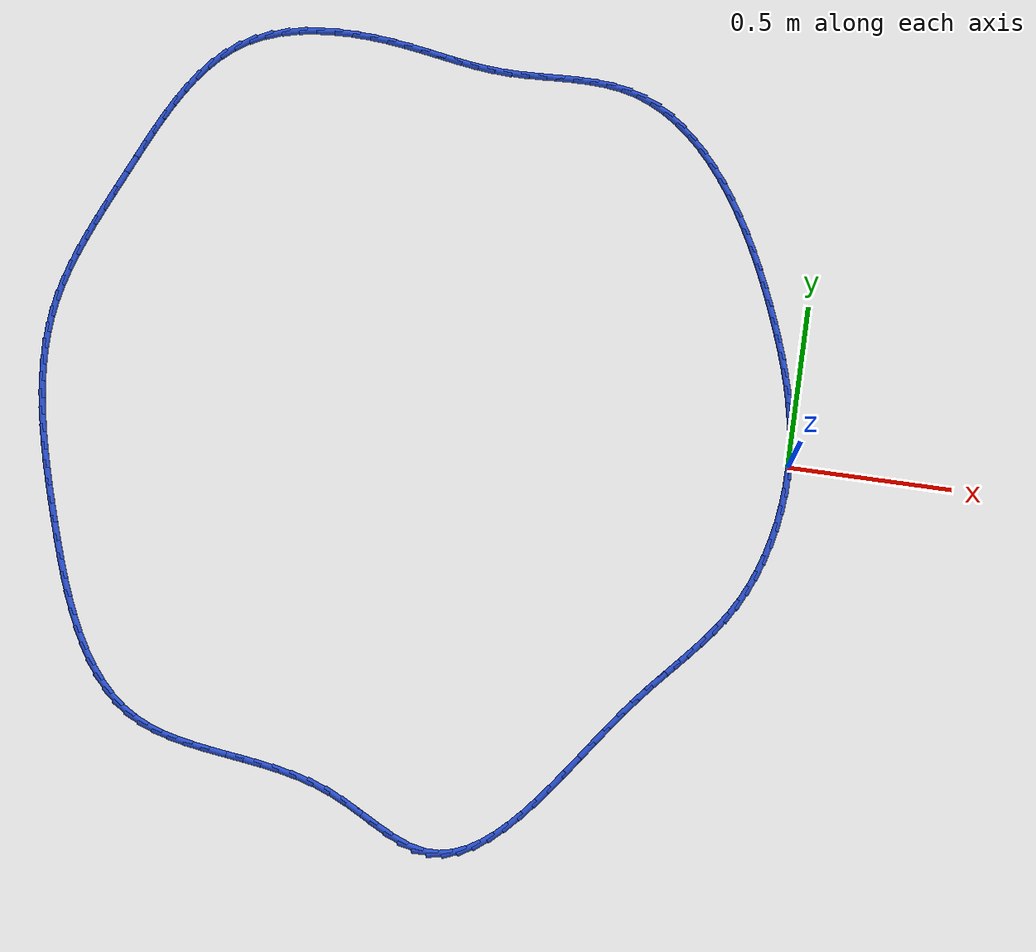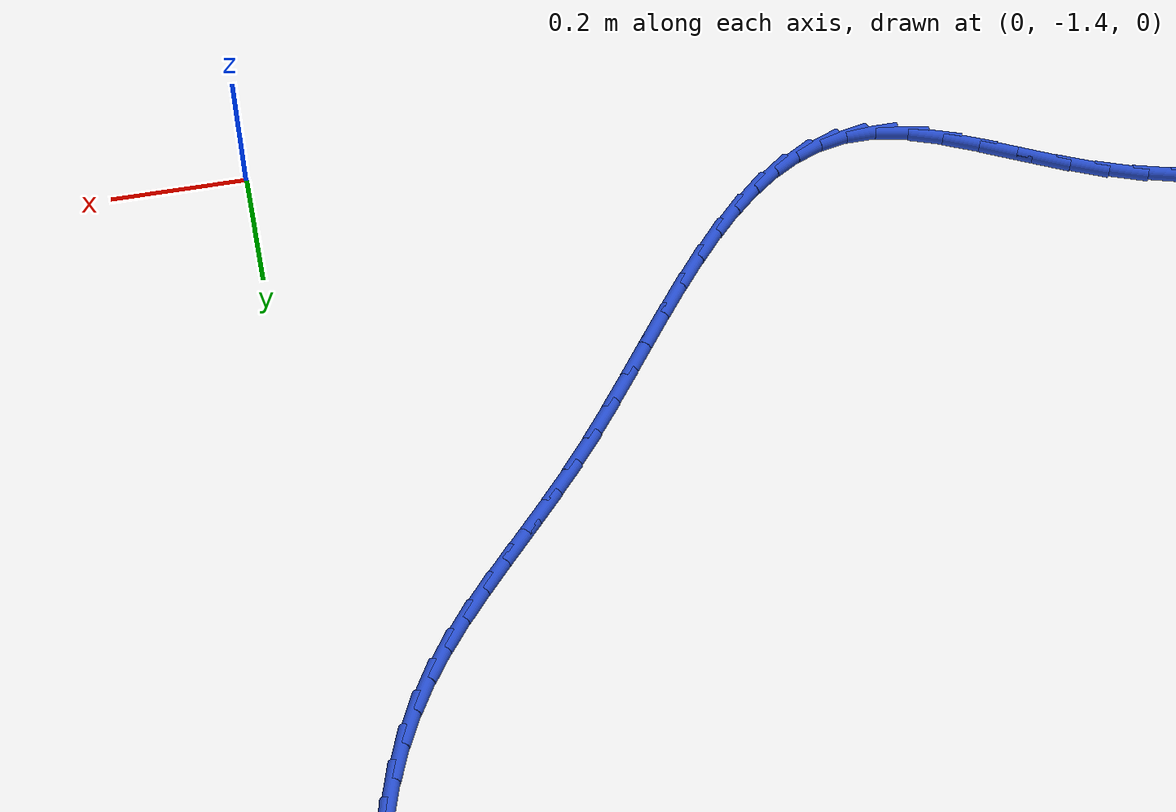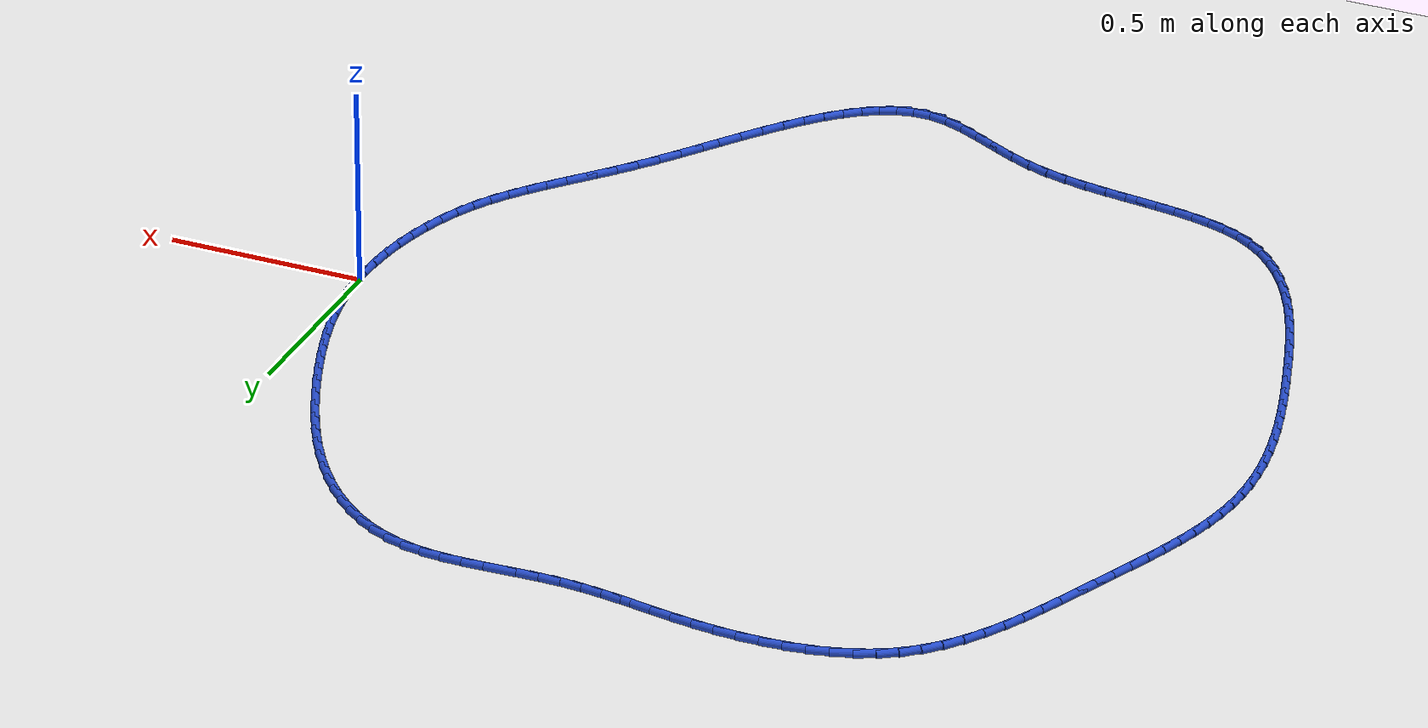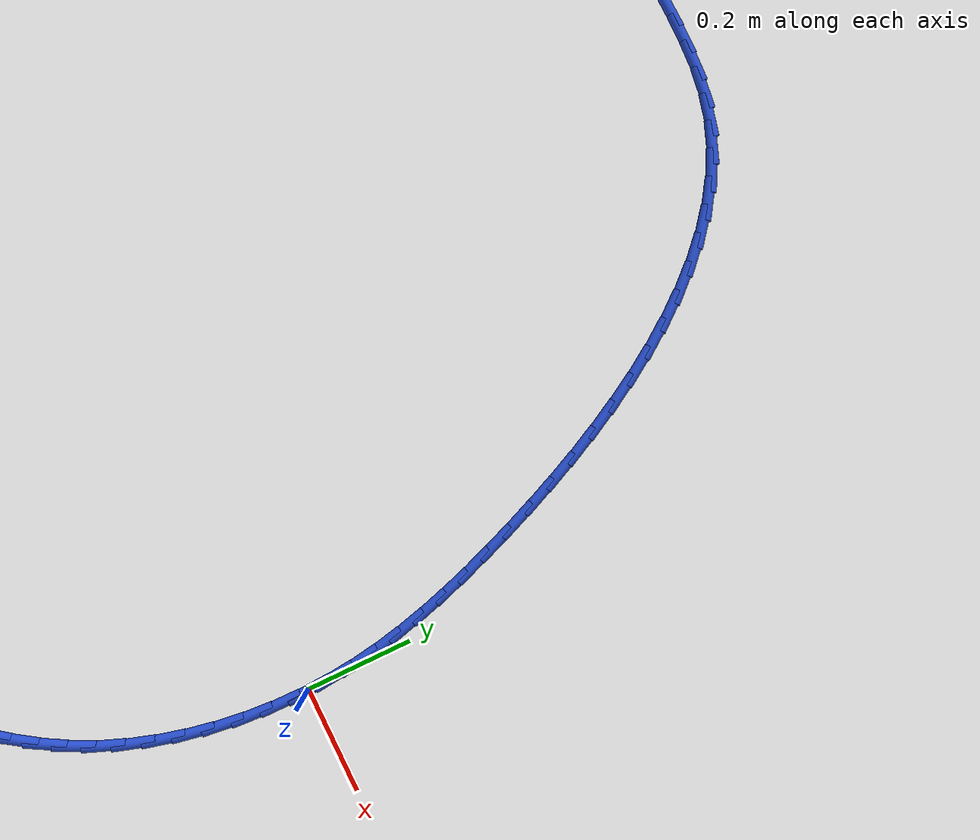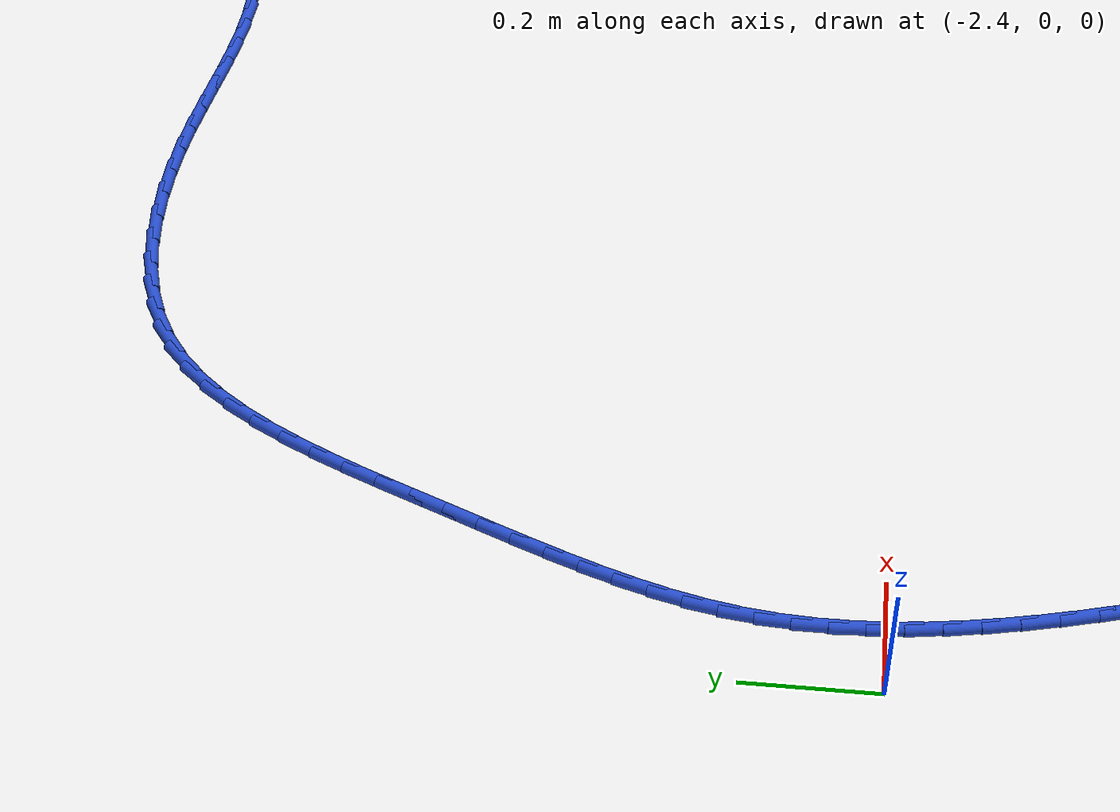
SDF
<sdf version="1.6">
 <world name="default">
  <light name="sun" type="directional">
   <pose>0 0 10 0 -0 0</pose>
   <diffuse>0.8 0.8 0.8 1</diffuse>
   <specular>0.2 0.2 0.2 1</specular>
   <attenuation>
    <range>1000</range>
    <constant>0.9</constant>
    <linear>0.01</linear>
    <quadratic>0.001</quadratic>
   </attenuation>
   <direction>-0.5 0.1 -0.9</direction>
  </light>
  <model name="ground_plane">
   <static>1</static>
   <link name="link">
    <collision name="collision">
     <geometry><plane><normal>0 0 1</normal><size>100 100</size></plane></geometry>
     <surface><friction><ode><mu>100</mu><mu2>50</mu2></ode></friction></surface>
    </collision>
    <visual name="visual">
     <cast_shadows>0</cast_shadows>
     <geometry><plane><normal>0 0 1</normal><size>100 100</size></plane></geometry>
     <material>
      <script><uri>file://media/materials/scripts/gazebo.material</uri><name>Gazebo/WhiteGlow</name></script>
     </material>
    </visual>
   </link>
  </model>
  <gravity>0 0 -9.8</gravity>
  <magnetic_field>6e-06 2.3e-05 -4.2e-05</magnetic_field>
  <atmosphere type="adiabatic"/>
  <physics name="default_physics" default="0" type="ode">
   <max_step_size>0.001</max_step_size>
   <real_time_factor>1</real_time_factor>
   <real_time_update_rate>1000</real_time_update_rate>
  </physics>
  <scene><ambient>0.4 0.4 0.4 1</ambient><background>0.7 0.7 0.7 1</background><shadows>1</shadows></scene>
  <spherical_coordinates>
   <surface_model>EARTH_WGS84</surface_model>
   <latitude_deg>0</latitude_deg>
   <longitude_deg>0</longitude_deg>
   <elevation>0</elevation>
   <heading_deg>0</heading_deg>
  </spherical_coordinates>
  <model name="line">
   <link name="link_0">
    <pose>-3.469446951953614e-17 -1.3877787807814457e-17 0.01 0 1.57 -1.5203196387642521</pose>
    <collision name="collision">
     <geometry><cylinder><radius>0.01</radius><length>0.08</length></cylinder></geometry>
    </collision>
    <visual name="visual">
     <material>
      <script><name>Gazebo/Blue</name><uri>file://media/materials/scripts/gazebo.material</uri></script>
     </material>
     <geometry><cylinder><radius>0.01</radius><length>0.08</length></cylinder></geometry>
    </visual>
   </link>
   <link name="link_1">
    <pose>-0.002669319300938437 0.05283729916652684 0.01 0 1.57 -1.4642558566457982</pose>
    <collision name="collision">
     <geometry><cylinder><radius>0.01</radius><length>0.08</length></cylinder></geometry>
    </collision>
    <visual name="visual">
     <material>
      <script><name>Gazebo/Blue</name><uri>file://media/materials/scripts/gazebo.material</uri></script>
     </material>
     <geometry><cylinder><radius>0.01</radius><length>0.08</length></cylinder></geometry>
    </visual>
   </link>
   <link name="link_2">
    <pose>-0.008244664585451691 0.1049699233846303 0.01 0 1.57 -1.4117139446794178</pose>
    <collision name="collision">
     <geometry><cylinder><radius>0.01</radius><length>0.08</length></cylinder></geometry>
    </collision>
    <visual name="visual">
     <material>
      <script><name>Gazebo/Blue</name><uri>file://media/materials/scripts/gazebo.material</uri></script>
     </material>
     <geometry><cylinder><radius>0.01</radius><length>0.08</length></cylinder></geometry>
    </visual>
   </link>
   <link name="link_3">
    <pose>-0.016528430032021937 0.15660208721732294 0.01 0 1.57 -1.3635422617413602</pose>
    <collision name="collision">
     <geometry><cylinder><radius>0.01</radius><length>0.08</length></cylinder></geometry>
    </collision>
    <visual name="visual">
     <material>
      <script><name>Gazebo/Blue</name><uri>file://media/materials/scripts/gazebo.material</uri></script>
     </material>
     <geometry><cylinder><radius>0.01</radius><length>0.08</length></cylinder></geometry>
    </visual>
   </link>
   <link name="link_4">
    <pose>-0.027323009819131303 0.20793800522761732 0.01 0 1.57 -1.320373622092523</pose>
    <collision name="collision">
     <geometry><cylinder><radius>0.01</radius><length>0.08</length></cylinder></geometry>
    </collision>
    <visual name="visual">
     <material>
      <script><name>Gazebo/Blue</name><uri>file://media/materials/scripts/gazebo.material</uri></script>
     </material>
     <geometry><cylinder><radius>0.01</radius><length>0.08</length></cylinder></geometry>
    </visual>
   </link>
   <link name="link_5">
    <pose>-0.04043079812526196 0.2591818919785262 0.01 0 1.57 -1.2826195614353006</pose>
    <collision name="collision">
     <geometry><cylinder><radius>0.01</radius><length>0.08</length></cylinder></geometry>
    </collision>
    <visual name="visual">
     <material>
      <script><name>Gazebo/Blue</name><uri>file://media/materials/scripts/gazebo.material</uri></script>
     </material>
     <geometry><cylinder><radius>0.01</radius><length>0.08</length></cylinder></geometry>
    </visual>
   </link>
   <link name="link_6">
    <pose>-0.05565418912889604 0.31053796203306216 0.01 0 1.57 -1.2504880694065612</pose>
    <collision name="collision">
     <geometry><cylinder><radius>0.01</radius><length>0.08</length></cylinder></geometry>
    </collision>
    <visual name="visual">
     <material>
      <script><name>Gazebo/Blue</name><uri>file://media/materials/scripts/gazebo.material</uri></script>
     </material>
     <geometry><cylinder><radius>0.01</radius><length>0.08</length></cylinder></geometry>
    </visual>
   </link>
   <link name="link_7">
    <pose>-0.07279557700851565 0.3622104299542375 0.01 0 1.57 -1.2240154850599632</pose>
    <collision name="collision">
     <geometry><cylinder><radius>0.01</radius><length>0.08</length></cylinder></geometry>
    </collision>
    <visual name="visual">
     <material>
      <script><name>Gazebo/Blue</name><uri>file://media/materials/scripts/gazebo.material</uri></script>
     </material>
     <geometry><cylinder><radius>0.01</radius><length>0.08</length></cylinder></geometry>
    </visual>
   </link>
   <link name="link_8">
    <pose>-0.09165735594260299 0.41440351030506517 0.01 0 1.57 -1.2027747211286963</pose>
    <collision name="collision">
     <geometry><cylinder><radius>0.01</radius><length>0.08</length></cylinder></geometry>
    </collision>
    <visual name="visual">
     <material>
      <script><name>Gazebo/Blue</name><uri>file://media/materials/scripts/gazebo.material</uri></script>
     </material>
     <geometry><cylinder><radius>0.01</radius><length>0.08</length></cylinder></geometry>
    </visual>
   </link>
   <link name="link_9">
    <pose>-0.11205191719885056 0.46729549473235976 0.01 0 1.57 -1.182195684446897</pose>
    <collision name="collision">
     <geometry><cylinder><radius>0.01</radius><length>0.08</length></cylinder></geometry>
    </collision>
    <visual name="visual">
     <material>
      <script><name>Gazebo/Blue</name><uri>file://media/materials/scripts/gazebo.material</uri></script>
     </material>
     <geometry><cylinder><radius>0.01</radius><length>0.08</length></cylinder></geometry>
    </visual>
   </link>
   <link name="link_10">
    <pose>-0.13392477181203818 0.5207194891499809 0.01 0 1.57 -1.1589195291376073</pose>
    <collision name="collision">
     <geometry><cylinder><radius>0.01</radius><length>0.08</length></cylinder></geometry>
    </collision>
    <visual name="visual">
     <material>
      <script><name>Gazebo/Blue</name><uri>file://media/materials/scripts/gazebo.material</uri></script>
     </material>
     <geometry><cylinder><radius>0.01</radius><length>0.08</length></cylinder></geometry>
    </visual>
   </link>
   <link name="link_11">
    <pose>-0.15731608827790985 0.5742631482833028 0.01 0 1.57 -1.132567049161847</pose>
    <collision name="collision">
     <geometry><cylinder><radius>0.01</radius><length>0.08</length></cylinder></geometry>
    </collision>
    <visual name="visual">
     <material>
      <script><name>Gazebo/Blue</name><uri>file://media/materials/scripts/gazebo.material</uri></script>
     </material>
     <geometry><cylinder><radius>0.01</radius><length>0.08</length></cylinder></geometry>
    </visual>
   </link>
   <link name="link_12">
    <pose>-0.18226805824399656 0.6275088807312389 0.01 0 1.57 -1.1027464000518488</pose>
    <collision name="collision">
     <geometry><cylinder><radius>0.01</radius><length>0.08</length></cylinder></geometry>
    </collision>
    <visual name="visual">
     <material>
      <script><name>Gazebo/Blue</name><uri>file://media/materials/scripts/gazebo.material</uri></script>
     </material>
     <geometry><cylinder><radius>0.01</radius><length>0.08</length></cylinder></geometry>
    </visual>
   </link>
   <link name="link_13">
    <pose>-0.2088228733578294 0.6800390950927037 0.01 0 1.57 -1.068977757885744</pose>
    <collision name="collision">
     <geometry><cylinder><radius>0.01</radius><length>0.08</length></cylinder></geometry>
    </collision>
    <visual name="visual">
     <material>
      <script><name>Gazebo/Blue</name><uri>file://media/materials/scripts/gazebo.material</uri></script>
     </material>
     <geometry><cylinder><radius>0.01</radius><length>0.08</length></cylinder></geometry>
    </visual>
   </link>
   <link name="link_14">
    <pose>-0.2370227252669392 0.7314361999666104 0.01 0 1.57 -1.0306831477319096</pose>
    <collision name="collision">
     <geometry><cylinder><radius>0.01</radius><length>0.08</length></cylinder></geometry>
    </collision>
    <visual name="visual">
     <material>
      <script><name>Gazebo/Blue</name><uri>file://media/materials/scripts/gazebo.material</uri></script>
     </material>
     <geometry><cylinder><radius>0.01</radius><length>0.08</length></cylinder></geometry>
    </visual>
   </link>
   <link name="link_15">
    <pose>-0.26690980561885735 0.7812826039518731 0.01 0 1.57 -0.9871768040926602</pose>
    <collision name="collision">
     <geometry><cylinder><radius>0.01</radius><length>0.08</length></cylinder></geometry>
    </collision>
    <visual name="visual">
     <material>
      <script><name>Gazebo/Blue</name><uri>file://media/materials/scripts/gazebo.material</uri></script>
     </material>
     <geometry><cylinder><radius>0.01</radius><length>0.08</length></cylinder></geometry>
    </visual>
   </link>
   <link name="link_16">
    <pose>-0.2985263060611147 0.8291607156474057 0.01 0 1.57 -0.9376595781071306</pose>
    <collision name="collision">
     <geometry><cylinder><radius>0.01</radius><length>0.08</length></cylinder></geometry>
    </collision>
    <visual name="visual">
     <material>
      <script><name>Gazebo/Blue</name><uri>file://media/materials/scripts/gazebo.material</uri></script>
     </material>
     <geometry><cylinder><radius>0.01</radius><length>0.08</length></cylinder></geometry>
    </visual>
   </link>
   <link name="link_17">
    <pose>-0.33191441824124207 0.8746529436521213 0.01 0 1.57 -0.8812235999409279</pose>
    <collision name="collision">
     <geometry><cylinder><radius>0.01</radius><length>0.08</length></cylinder></geometry>
    </collision>
    <visual name="visual">
     <material>
      <script><name>Gazebo/Blue</name><uri>file://media/materials/scripts/gazebo.material</uri></script>
     </material>
     <geometry><cylinder><radius>0.01</radius><length>0.08</length></cylinder></geometry>
    </visual>
   </link>
   <link name="link_18">
    <pose>-0.3671163338067708 0.9173416965649344 0.01 0 1.57 -0.8168775620754979</pose>
    <collision name="collision">
     <geometry><cylinder><radius>0.01</radius><length>0.08</length></cylinder></geometry>
    </collision>
    <visual name="visual">
     <material>
      <script><name>Gazebo/Blue</name><uri>file://media/materials/scripts/gazebo.material</uri></script>
     </material>
     <geometry><cylinder><radius>0.01</radius><length>0.08</length></cylinder></geometry>
    </visual>
   </link>
   <link name="link_19">
    <pose>-0.4041742444052318 0.9568093829847586 0.01 0 1.57 -0.743608460455484</pose>
    <collision name="collision">
     <geometry><cylinder><radius>0.01</radius><length>0.08</length></cylinder></geometry>
    </collision>
    <visual name="visual">
     <material>
      <script><name>Gazebo/Blue</name><uri>file://media/materials/scripts/gazebo.material</uri></script>
     </material>
     <geometry><cylinder><radius>0.01</radius><length>0.08</length></cylinder></geometry>
    </visual>
   </link>
   <link name="link_20">
    <pose>-0.4431303416841561 0.9926384115105074 0.01 0 1.57 -0.6605006993845354</pose>
    <collision name="collision">
     <geometry><cylinder><radius>0.01</radius><length>0.08</length></cylinder></geometry>
    </collision>
    <visual name="visual">
     <material>
      <script><name>Gazebo/Blue</name><uri>file://media/materials/scripts/gazebo.material</uri></script>
     </material>
     <geometry><cylinder><radius>0.01</radius><length>0.08</length></cylinder></geometry>
    </visual>
   </link>
   <link name="link_21">
    <pose>-0.48402681729107483 1.024411190741095 0.01 0 1.57 -0.5669329177722653</pose>
    <collision name="collision">
     <geometry><cylinder><radius>0.01</radius><length>0.08</length></cylinder></geometry>
    </collision>
    <visual name="visual">
     <material>
      <script><name>Gazebo/Blue</name><uri>file://media/materials/scripts/gazebo.material</uri></script>
     </material>
     <geometry><cylinder><radius>0.01</radius><length>0.08</length></cylinder></geometry>
    </visual>
   </link>
   <link name="link_22">
    <pose>-0.5269058628735188 1.0517101292754347 0.01 0 1.57 -0.4628563224764566</pose>
    <collision name="collision">
     <geometry><cylinder><radius>0.01</radius><length>0.08</length></cylinder></geometry>
    </collision>
    <visual name="visual">
     <material>
      <script><name>Gazebo/Blue</name><uri>file://media/materials/scripts/gazebo.material</uri></script>
     </material>
     <geometry><cylinder><radius>0.01</radius><length>0.08</length></cylinder></geometry>
    </visual>
   </link>
   <link name="link_23">
    <pose>-0.5718096700790193 1.0741176357124411 0.01 0 1.57 -0.3491133038659414</pose>
    <collision name="collision">
     <geometry><cylinder><radius>0.01</radius><length>0.08</length></cylinder></geometry>
    </collision>
    <visual name="visual">
     <material>
      <script><name>Gazebo/Blue</name><uri>file://media/materials/scripts/gazebo.material</uri></script>
     </material>
     <geometry><cylinder><radius>0.01</radius><length>0.08</length></cylinder></geometry>
    </visual>
   </link>
   <link name="link_24">
    <pose>-0.6187804305551072 1.091216118651027 0.01 0 1.57 -0.22824404134933768</pose>
    <collision name="collision">
     <geometry><cylinder><radius>0.01</radius><length>0.08</length></cylinder></geometry>
    </collision>
    <visual name="visual">
     <material>
      <script><name>Gazebo/Blue</name><uri>file://media/materials/scripts/gazebo.material</uri></script>
     </material>
     <geometry><cylinder><radius>0.01</radius><length>0.08</length></cylinder></geometry>
    </visual>
   </link>
   <link name="link_25">
    <pose>-0.6678528323740427 1.1026152399058893 0.01 0 1.57 -0.11864713775809461</pose>
    <collision name="collision">
     <geometry><cylinder><radius>0.01</radius><length>0.08</length></cylinder></geometry>
    </collision>
    <visual name="visual">
     <material>
      <script><name>Gazebo/Blue</name><uri>file://media/materials/scripts/gazebo.material</uri></script>
     </material>
     <geometry><cylinder><radius>0.01</radius><length>0.08</length></cylinder></geometry>
    </visual>
   </link>
   <link name="link_26">
    <pose>-0.7188496284176339 1.1086944164109658 0.01 0 1.57 -0.038020621731585054</pose>
    <collision name="collision">
     <geometry><cylinder><radius>0.01</radius><length>0.08</length></cylinder></geometry>
    </collision>
    <visual name="visual">
     <material>
      <script><name>Gazebo/Blue</name><uri>file://media/materials/scripts/gazebo.material</uri></script>
     </material>
     <geometry><cylinder><radius>0.01</radius><length>0.08</length></cylinder></geometry>
    </visual>
   </link>
   <link name="link_27">
    <pose>-0.7713571521655634 1.1106917476280267 0.01 0 1.57 0.014950870576087174</pose>
    <collision name="collision">
     <geometry><cylinder><radius>0.01</radius><length>0.08</length></cylinder></geometry>
    </collision>
    <visual name="visual">
     <material>
      <script><name>Gazebo/Blue</name><uri>file://media/materials/scripts/gazebo.material</uri></script>
     </material>
     <geometry><cylinder><radius>0.01</radius><length>0.08</length></cylinder></geometry>
    </visual>
   </link>
   <link name="link_28">
    <pose>-0.8249493183250272 1.109890438381835 0.01 0 1.57 0.04267847432447619</pose>
    <collision name="collision">
     <geometry><cylinder><radius>0.01</radius><length>0.08</length></cylinder></geometry>
    </collision>
    <visual name="visual">
     <material>
      <script><name>Gazebo/Blue</name><uri>file://media/materials/scripts/gazebo.material</uri></script>
     </material>
     <geometry><cylinder><radius>0.01</radius><length>0.08</length></cylinder></geometry>
    </visual>
   </link>
   <link name="link_29">
    <pose>-0.8792000416032212 1.1075736934971545 0.01 0 1.57 0.046750532869200695</pose>
    <collision name="collision">
     <geometry><cylinder><radius>0.01</radius><length>0.08</length></cylinder></geometry>
    </collision>
    <visual name="visual">
     <material>
      <script><name>Gazebo/Blue</name><uri>file://media/materials/scripts/gazebo.material</uri></script>
     </material>
     <geometry><cylinder><radius>0.01</radius><length>0.08</length></cylinder></geometry>
    </visual>
   </link>
   <link name="link_30">
    <pose>-0.9336832367073407 1.1050247177987487 0.01 0 1.57 0.027585802681831847</pose>
    <collision name="collision">
     <geometry><cylinder><radius>0.01</radius><length>0.08</length></cylinder></geometry>
    </collision>
    <visual name="visual">
     <material>
      <script><name>Gazebo/Blue</name><uri>file://media/materials/scripts/gazebo.material</uri></script>
     </material>
     <geometry><cylinder><radius>0.01</radius><length>0.08</length></cylinder></geometry>
    </visual>
   </link>
   <link name="link_31">
    <pose>-0.9879728183445817 1.1035267161113809 0.01 0 1.57 -0.015559955053411446</pose>
    <collision name="collision">
     <geometry><cylinder><radius>0.01</radius><length>0.08</length></cylinder></geometry>
    </collision>
    <visual name="visual">
     <material>
      <script><name>Gazebo/Blue</name><uri>file://media/materials/scripts/gazebo.material</uri></script>
     </material>
     <geometry><cylinder><radius>0.01</radius><length>0.08</length></cylinder></geometry>
    </visual>
   </link>
   <link name="link_32">
    <pose>-1.0416430713244609 1.1043618902384897 0.01 0 1.57 -0.07422381804057417</pose>
    <collision name="collision">
     <geometry><cylinder><radius>0.01</radius><length>0.08</length></cylinder></geometry>
    </collision>
    <visual name="visual">
     <material>
      <script><name>Gazebo/Blue</name><uri>file://media/materials/scripts/gazebo.material</uri></script>
     </material>
     <geometry><cylinder><radius>0.01</radius><length>0.08</length></cylinder></geometry>
    </visual>
   </link>
   <link name="link_33">
    <pose>-1.094461249715894 1.1082894723303038 0.01 0 1.57 -0.12192668076725774</pose>
    <collision name="collision">
     <geometry><cylinder><radius>0.01</radius><length>0.08</length></cylinder></geometry>
    </collision>
    <visual name="visual">
     <material>
      <script><name>Gazebo/Blue</name><uri>file://media/materials/scripts/gazebo.material</uri></script>
     </material>
     <geometry><cylinder><radius>0.01</radius><length>0.08</length></cylinder></geometry>
    </visual>
   </link>
   <link name="link_34">
    <pose>-1.1467030007730448 1.1146908885144284 0.01 0 1.57 -0.15319002748215022</pose>
    <collision name="collision">
     <geometry><cylinder><radius>0.01</radius><length>0.08</length></cylinder></geometry>
    </collision>
    <visual name="visual">
     <material>
      <script><name>Gazebo/Blue</name><uri>file://media/materials/scripts/gazebo.material</uri></script>
     </material>
     <geometry><cylinder><radius>0.01</radius><length>0.08</length></cylinder></geometry>
    </visual>
   </link>
   <link name="link_35">
    <pose>-1.1987267103418553 1.1227233334901834 0.01 0 1.57 -0.16751021772606114</pose>
    <collision name="collision">
     <geometry><cylinder><radius>0.01</radius><length>0.08</length></cylinder></geometry>
    </collision>
    <visual name="visual">
     <material>
      <script><name>Gazebo/Blue</name><uri>file://media/materials/scripts/gazebo.material</uri></script>
     </material>
     <geometry><cylinder><radius>0.01</radius><length>0.08</length></cylinder></geometry>
    </visual>
   </link>
   <link name="link_36">
    <pose>-1.2508907642682685 1.1315440019568883 0.01 0 1.57 -0.16494462611945873</pose>
    <collision name="collision">
     <geometry><cylinder><radius>0.01</radius><length>0.08</length></cylinder></geometry>
    </collision>
    <visual name="visual">
     <material>
      <script><name>Gazebo/Blue</name><uri>file://media/materials/scripts/gazebo.material</uri></script>
     </material>
     <geometry><cylinder><radius>0.01</radius><length>0.08</length></cylinder></geometry>
    </visual>
   </link>
   <link name="link_37">
    <pose>-1.3035535483982286 1.1403100886138635 0.01 0 1.57 -0.14597798357198347</pose>
    <collision name="collision">
     <geometry><cylinder><radius>0.01</radius><length>0.08</length></cylinder></geometry>
    </collision>
    <visual name="visual">
     <material>
      <script><name>Gazebo/Blue</name><uri>file://media/materials/scripts/gazebo.material</uri></script>
     </material>
     <geometry><cylinder><radius>0.01</radius><length>0.08</length></cylinder></geometry>
    </visual>
   </link>
   <link name="link_38">
    <pose>-1.3570734485776779 1.1481787881604293 0.01 0 1.57 -0.11190379082181612</pose>
    <collision name="collision">
     <geometry><cylinder><radius>0.01</radius><length>0.08</length></cylinder></geometry>
    </collision>
    <visual name="visual">
     <material>
      <script><name>Gazebo/Blue</name><uri>file://media/materials/scripts/gazebo.material</uri></script>
     </material>
     <geometry><cylinder><radius>0.01</radius><length>0.08</length></cylinder></geometry>
    </visual>
   </link>
   <link name="link_39">
    <pose>-1.4117688533883204 1.154325088339026 0.01 0 1.57 -0.06889897911702023</pose>
    <collision name="collision">
     <geometry><cylinder><radius>0.01</radius><length>0.08</length></cylinder></geometry>
    </collision>
    <visual name="visual">
     <material>
      <script><name>Gazebo/Blue</name><uri>file://media/materials/scripts/gazebo.material</uri></script>
     </material>
     <geometry><cylinder><radius>0.01</radius><length>0.08</length></cylinder></geometry>
    </visual>
   </link>
   <link name="link_40">
    <pose>-1.46741591864718 1.158165192663913 0.01 0 1.57 -0.02007039555825768</pose>
    <collision name="collision">
     <geometry><cylinder><radius>0.01</radius><length>0.08</length></cylinder></geometry>
    </collision>
    <visual name="visual">
     <material>
      <script><name>Gazebo/Blue</name><uri>file://media/materials/scripts/gazebo.material</uri></script>
     </material>
     <geometry><cylinder><radius>0.01</radius><length>0.08</length></cylinder></geometry>
    </visual>
   </link>
   <link name="link_41">
    <pose>-1.5234004052836085 1.1592889743540893 0.01 0 1.57 0.035871069887644304</pose>
    <collision name="collision">
     <geometry><cylinder><radius>0.01</radius><length>0.08</length></cylinder></geometry>
    </collision>
    <visual name="visual">
     <material>
      <script><name>Gazebo/Blue</name><uri>file://media/materials/scripts/gazebo.material</uri></script>
     </material>
     <geometry><cylinder><radius>0.01</radius><length>0.08</length></cylinder></geometry>
    </visual>
   </link>
   <link name="link_42">
    <pose>-1.5790994757789174 1.1572901317040867 0.01 0 1.57 0.10054837489951907</pose>
    <collision name="collision">
     <geometry><cylinder><radius>0.01</radius><length>0.08</length></cylinder></geometry>
    </collision>
    <visual name="visual">
     <material>
      <script><name>Gazebo/Blue</name><uri>file://media/materials/scripts/gazebo.material</uri></script>
     </material>
     <geometry><cylinder><radius>0.01</radius><length>0.08</length></cylinder></geometry>
    </visual>
   </link>
   <link name="link_43">
    <pose>-1.6338902926144176 1.1517623630084355 0.01 0 1.57 0.17584135414790342</pose>
    <collision name="collision">
     <geometry><cylinder><radius>0.01</radius><length>0.08</length></cylinder></geometry>
    </collision>
    <visual name="visual">
     <material>
      <script><name>Gazebo/Blue</name><uri>file://media/materials/scripts/gazebo.material</uri></script>
     </material>
     <geometry><cylinder><radius>0.01</radius><length>0.08</length></cylinder></geometry>
    </visual>
   </link>
   <link name="link_44">
    <pose>-1.6871500182714212 1.1422993665616665 0.01 0 1.57 0.2638205413015839</pose>
    <collision name="collision">
     <geometry><cylinder><radius>0.01</radius><length>0.08</length></cylinder></geometry>
    </collision>
    <visual name="visual">
     <material>
      <script><name>Gazebo/Blue</name><uri>file://media/materials/scripts/gazebo.material</uri></script>
     </material>
     <geometry><cylinder><radius>0.01</radius><length>0.08</length></cylinder></geometry>
    </visual>
   </link>
   <link name="link_45">
    <pose>-1.738255815231239 1.1284948406583115 0.01 0 1.57 0.36652960835199705</pose>
    <collision name="collision">
     <geometry><cylinder><radius>0.01</radius><length>0.08</length></cylinder></geometry>
    </collision>
    <visual name="visual">
     <material>
      <script><name>Gazebo/Blue</name><uri>file://media/materials/scripts/gazebo.material</uri></script>
     </material>
     <geometry><cylinder><radius>0.01</radius><length>0.08</length></cylinder></geometry>
    </visual>
   </link>
   <link name="link_46">
    <pose>-1.7865848459751832 1.1099424835929008 0.01 0 1.57 0.48551305636139785</pose>
    <collision name="collision">
     <geometry><cylinder><radius>0.01</radius><length>0.08</length></cylinder></geometry>
    </collision>
    <visual name="visual">
     <material>
      <script><name>Gazebo/Blue</name><uri>file://media/materials/scripts/gazebo.material</uri></script>
     </material>
     <geometry><cylinder><radius>0.01</radius><length>0.08</length></cylinder></geometry>
    </visual>
   </link>
   <link name="link_47">
    <pose>-1.8315142729845646 1.086235993659966 0.01 0 1.57 0.6163957369088132</pose>
    <collision name="collision">
     <geometry><cylinder><radius>0.01</radius><length>0.08</length></cylinder></geometry>
    </collision>
    <visual name="visual">
     <material>
      <script><name>Gazebo/Blue</name><uri>file://media/materials/scripts/gazebo.material</uri></script>
     </material>
     <geometry><cylinder><radius>0.01</radius><length>0.08</length></cylinder></geometry>
    </visual>
   </link>
   <link name="link_48">
    <pose>-1.8725887787111495 1.0571354574199792 0.01 0 1.57 0.7381308289066679</pose>
    <collision name="collision">
     <geometry><cylinder><radius>0.01</radius><length>0.08</length></cylinder></geometry>
    </collision>
    <visual name="visual">
     <material>
      <script><name>Gazebo/Blue</name><uri>file://media/materials/scripts/gazebo.material</uri></script>
     </material>
     <geometry><cylinder><radius>0.01</radius><length>0.08</length></cylinder></geometry>
    </visual>
   </link>
   <link name="link_49">
    <pose>-1.9100315981296636 1.0230749299002155 0.01 0 1.57 0.8433005206234342</pose>
    <collision name="collision">
     <geometry><cylinder><radius>0.01</radius><length>0.08</length></cylinder></geometry>
    </collision>
    <visual name="visual">
     <material>
      <script><name>Gazebo/Blue</name><uri>file://media/materials/scripts/gazebo.material</uri></script>
     </material>
     <geometry><cylinder><radius>0.01</radius><length>0.08</length></cylinder></geometry>
    </visual>
   </link>
   <link name="link_50">
    <pose>-1.9442377492196126 0.9846590886286914 0.01 0 1.57 0.9312586306665619</pose>
    <collision name="collision">
     <geometry><cylinder><radius>0.01</radius><length>0.08</length></cylinder></geometry>
    </collision>
    <visual name="visual">
     <material>
      <script><name>Gazebo/Blue</name><uri>file://media/materials/scripts/gazebo.material</uri></script>
     </material>
     <geometry><cylinder><radius>0.01</radius><length>0.08</length></cylinder></geometry>
    </visual>
   </link>
   <link name="link_51">
    <pose>-1.9756022499729622 0.9424926111458028 0.01 0 1.57 1.0027694228958193</pose>
    <collision name="collision">
     <geometry><cylinder><radius>0.01</radius><length>0.08</length></cylinder></geometry>
    </collision>
    <visual name="visual">
     <material>
      <script><name>Gazebo/Blue</name><uri>file://media/materials/scripts/gazebo.material</uri></script>
     </material>
     <geometry><cylinder><radius>0.01</radius><length>0.08</length></cylinder></geometry>
    </visual>
   </link>
   <link name="link_52">
    <pose>-2.0045201183816803 0.8971801749919444 0.01 0 1.57 1.059224163391763</pose>
    <collision name="collision">
     <geometry><cylinder><radius>0.01</radius><length>0.08</length></cylinder></geometry>
    </collision>
    <visual name="visual">
     <material>
      <script><name>Gazebo/Blue</name><uri>file://media/materials/scripts/gazebo.material</uri></script>
     </material>
     <geometry><cylinder><radius>0.01</radius><length>0.08</length></cylinder></geometry>
    </visual>
   </link>
   <link name="link_53">
    <pose>-2.031386372437734 0.8493264577075127 0.01 0 1.57 1.1021083485322976</pose>
    <collision name="collision">
     <geometry><cylinder><radius>0.01</radius><length>0.08</length></cylinder></geometry>
    </collision>
    <visual name="visual">
     <material>
      <script><name>Gazebo/Blue</name><uri>file://media/materials/scripts/gazebo.material</uri></script>
     </material>
     <geometry><cylinder><radius>0.01</radius><length>0.08</length></cylinder></geometry>
    </visual>
   </link>
   <link name="link_54">
    <pose>-2.05659603013309 0.7995361368329025 0.01 0 1.57 1.1327079535896718</pose>
    <collision name="collision">
     <geometry><cylinder><radius>0.01</radius><length>0.08</length></cylinder></geometry>
    </collision>
    <visual name="visual">
     <material>
      <script><name>Gazebo/Blue</name><uri>file://media/materials/scripts/gazebo.material</uri></script>
     </material>
     <geometry><cylinder><radius>0.01</radius><length>0.08</length></cylinder></geometry>
    </visual>
   </link>
   <link name="link_55">
    <pose>-2.0805441094597152 0.748413889908509 0.01 0 1.57 1.1519714500456442</pose>
    <collision name="collision">
     <geometry><cylinder><radius>0.01</radius><length>0.08</length></cylinder></geometry>
    </collision>
    <visual name="visual">
     <material>
      <script><name>Gazebo/Blue</name><uri>file://media/materials/scripts/gazebo.material</uri></script>
     </material>
     <geometry><cylinder><radius>0.01</radius><length>0.08</length></cylinder></geometry>
    </visual>
   </link>
   <link name="link_56">
    <pose>-2.1036256284095782 0.6965643944747287 0.01 0 1.57 1.1604517465477318</pose>
    <collision name="collision">
     <geometry><cylinder><radius>0.01</radius><length>0.08</length></cylinder></geometry>
    </collision>
    <visual name="visual">
     <material>
      <script><name>Gazebo/Blue</name><uri>file://media/materials/scripts/gazebo.material</uri></script>
     </material>
     <geometry><cylinder><radius>0.01</radius><length>0.08</length></cylinder></geometry>
    </visual>
   </link>
   <link name="link_57">
    <pose>-2.1262356049746445 0.6445923280719562 0.01 0 1.57 1.1592859076343291</pose>
    <collision name="collision">
     <geometry><cylinder><radius>0.01</radius><length>0.08</length></cylinder></geometry>
    </collision>
    <visual name="visual">
     <material>
      <script><name>Gazebo/Blue</name><uri>file://media/materials/scripts/gazebo.material</uri></script>
     </material>
     <geometry><cylinder><radius>0.01</radius><length>0.08</length></cylinder></geometry>
    </visual>
   </link>
   <link name="link_58">
    <pose>-2.148724704841484 0.5930624234870996 0.01 0 1.57 1.1590130175164648</pose>
    <collision name="collision">
     <geometry><cylinder><radius>0.01</radius><length>0.08</length></cylinder></geometry>
    </collision>
    <visual name="visual">
     <material>
      <script><name>Gazebo/Blue</name><uri>file://media/materials/scripts/gazebo.material</uri></script>
     </material>
     <geometry><cylinder><radius>0.01</radius><length>0.08</length></cylinder></geometry>
    </visual>
   </link>
   <link name="link_59">
    <pose>-2.1709750748412047 0.5421174541518946 0.01 0 1.57 1.1662025654143588</pose>
    <collision name="collision">
     <geometry><cylinder><radius>0.01</radius><length>0.08</length></cylinder></geometry>
    </collision>
    <visual name="visual">
     <material>
      <script><name>Gazebo/Blue</name><uri>file://media/materials/scripts/gazebo.material</uri></script>
     </material>
     <geometry><cylinder><radius>0.01</radius><length>0.08</length></cylinder></geometry>
    </visual>
   </link>
   <link name="link_60">
    <pose>-2.192587540796242 0.4916468290282597 0.01 0 1.57 1.1812494543171992</pose>
    <collision name="collision">
     <geometry><cylinder><radius>0.01</radius><length>0.08</length></cylinder></geometry>
    </collision>
    <visual name="visual">
     <material>
      <script><name>Gazebo/Blue</name><uri>file://media/materials/scripts/gazebo.material</uri></script>
     </material>
     <geometry><cylinder><radius>0.01</radius><length>0.08</length></cylinder></geometry>
    </visual>
   </link>
   <link name="link_61">
    <pose>-2.2131590971582265 0.44153650645336784 0.01 0 1.57 1.2045110507998458</pose>
    <collision name="collision">
     <geometry><cylinder><radius>0.01</radius><length>0.08</length></cylinder></geometry>
    </collision>
    <visual name="visual">
     <material>
      <script><name>Gazebo/Blue</name><uri>file://media/materials/scripts/gazebo.material</uri></script>
     </material>
     <geometry><cylinder><radius>0.01</radius><length>0.08</length></cylinder></geometry>
    </visual>
   </link>
   <link name="link_62">
    <pose>-2.2322867383787863 0.39167244476439356 0.01 0 1.57 1.2363700536269717</pose>
    <collision name="collision">
     <geometry><cylinder><radius>0.01</radius><length>0.08</length></cylinder></geometry>
    </collision>
    <visual name="visual">
     <material>
      <script><name>Gazebo/Blue</name><uri>file://media/materials/scripts/gazebo.material</uri></script>
     </material>
     <geometry><cylinder><radius>0.01</radius><length>0.08</length></cylinder></geometry>
    </visual>
   </link>
   <link name="link_63">
    <pose>-2.249567458909552 0.34194060229850987 0.01 0 1.57 1.277187404085638</pose>
    <collision name="collision">
     <geometry><cylinder><radius>0.01</radius><length>0.08</length></cylinder></geometry>
    </collision>
    <visual name="visual">
     <material>
      <script><name>Gazebo/Blue</name><uri>file://media/materials/scripts/gazebo.material</uri></script>
     </material>
     <geometry><cylinder><radius>0.01</radius><length>0.08</length></cylinder></geometry>
    </visual>
   </link>
   <link name="link_64">
    <pose>-2.2645982532021516 0.2922269373928913 0.01 0 1.57 1.327226247220401</pose>
    <collision name="collision">
     <geometry><cylinder><radius>0.01</radius><length>0.08</length></cylinder></geometry>
    </collision>
    <visual name="visual">
     <material>
      <script><name>Gazebo/Blue</name><uri>file://media/materials/scripts/gazebo.material</uri></script>
     </material>
     <geometry><cylinder><radius>0.01</radius><length>0.08</length></cylinder></geometry>
    </visual>
   </link>
   <link name="link_65">
    <pose>-2.2769761157082145 0.24241740838471137 0.01 0 1.57 1.3865440265792146</pose>
    <collision name="collision">
     <geometry><cylinder><radius>0.01</radius><length>0.08</length></cylinder></geometry>
    </collision>
    <visual name="visual">
     <material>
      <script><name>Gazebo/Blue</name><uri>file://media/materials/scripts/gazebo.material</uri></script>
     </material>
     <geometry><cylinder><radius>0.01</radius><length>0.08</length></cylinder></geometry>
    </visual>
   </link>
   <link name="link_66">
    <pose>-2.2862980408793696 0.19239797361114325 0.01 0 1.57 1.4530764467393782</pose>
    <collision name="collision">
     <geometry><cylinder><radius>0.01</radius><length>0.08</length></cylinder></geometry>
    </collision>
    <visual name="visual">
     <material>
      <script><name>Gazebo/Blue</name><uri>file://media/materials/scripts/gazebo.material</uri></script>
     </material>
     <geometry><cylinder><radius>0.01</radius><length>0.08</length></cylinder></geometry>
    </visual>
   </link>
   <link name="link_67">
    <pose>-2.292250319844443 0.14206868322147945 0.01 0 1.57 1.5177095136458807</pose>
    <collision name="collision">
     <geometry><cylinder><radius>0.01</radius><length>0.08</length></cylinder></geometry>
    </collision>
    <visual name="visual">
     <material>
      <script><name>Gazebo/Blue</name><uri>file://media/materials/scripts/gazebo.material</uri></script>
     </material>
     <geometry><cylinder><radius>0.01</radius><length>0.08</length></cylinder></geometry>
    </visual>
   </link>
   <link name="link_68">
    <pose>-2.2949428775949183 0.0913964405670196 0.01 0 1.57 -1.5642953548803942</pose>
    <collision name="collision">
     <geometry><cylinder><radius>0.01</radius><length>0.08</length></cylinder></geometry>
    </collision>
    <visual name="visual">
     <material>
      <script><name>Gazebo/Blue</name><uri>file://media/materials/scripts/gazebo.material</uri></script>
     </material>
     <geometry><cylinder><radius>0.01</radius><length>0.08</length></cylinder></geometry>
    </visual>
   </link>
   <link name="link_69">
    <pose>-2.2946111381626344 0.040367953866985266 0.01 0 1.57 -1.510156496471147</pose>
    <collision name="collision">
     <geometry><cylinder><radius>0.01</radius><length>0.08</length></cylinder></geometry>
    </collision>
    <visual name="visual">
     <material>
      <script><name>Gazebo/Blue</name><uri>file://media/materials/scripts/gazebo.material</uri></script>
     </material>
     <geometry><cylinder><radius>0.01</radius><length>0.08</length></cylinder></geometry>
    </visual>
   </link>
   <link name="link_70">
    <pose>-2.2914905450423078 -0.011030065587987149 0.01 0 1.57 -1.4616544928749542</pose>
    <collision name="collision">
     <geometry><cylinder><radius>0.01</radius><length>0.08</length></cylinder></geometry>
    </collision>
    <visual name="visual">
     <material>
      <script><name>Gazebo/Blue</name><uri>file://media/materials/scripts/gazebo.material</uri></script>
     </material>
     <geometry><cylinder><radius>0.01</radius><length>0.08</length></cylinder></geometry>
    </visual>
   </link>
   <link name="link_71">
    <pose>-2.285816541728657 -0.0628109065072596 0.01 0 1.57 -1.418807091040675</pose>
    <collision name="collision">
     <geometry><cylinder><radius>0.01</radius><length>0.08</length></cylinder></geometry>
    </collision>
    <visual name="visual">
     <material>
      <script><name>Gazebo/Blue</name><uri>file://media/materials/scripts/gazebo.material</uri></script>
     </material>
     <geometry><cylinder><radius>0.01</radius><length>0.08</length></cylinder></geometry>
    </visual>
   </link>
   <link name="link_72">
    <pose>-2.277824571716404 -0.11498785760019514 0.01 0 1.57 -1.3815098685664464</pose>
    <collision name="collision">
     <geometry><cylinder><radius>0.01</radius><length>0.08</length></cylinder></geometry>
    </collision>
    <visual name="visual">
     <material>
      <script><name>Gazebo/Blue</name><uri>file://media/materials/scripts/gazebo.material</uri></script>
     </material>
     <geometry><cylinder><radius>0.01</radius><length>0.08</length></cylinder></geometry>
    </visual>
   </link>
   <link name="link_73">
    <pose>-2.267750078500266 -0.1675742075761576 0.01 0 1.57 -1.3495799342069044</pose>
    <collision name="collision">
     <geometry><cylinder><radius>0.01</radius><length>0.08</length></cylinder></geometry>
    </collision>
    <visual name="visual">
     <material>
      <script><name>Gazebo/Blue</name><uri>file://media/materials/scripts/gazebo.material</uri></script>
     </material>
     <geometry><cylinder><radius>0.01</radius><length>0.08</length></cylinder></geometry>
    </visual>
   </link>
   <link name="link_74">
    <pose>-2.255828505574962 -0.22058324514450783 0.01 0 1.57 -1.3227917927808153</pose>
    <collision name="collision">
     <geometry><cylinder><radius>0.01</radius><length>0.08</length></cylinder></geometry>
    </collision>
    <visual name="visual">
     <material>
      <script><name>Gazebo/Blue</name><uri>file://media/materials/scripts/gazebo.material</uri></script>
     </material>
     <geometry><cylinder><radius>0.01</radius><length>0.08</length></cylinder></geometry>
    </visual>
   </link>
   <link name="link_75">
    <pose>-2.2422952964352105 -0.2740282590146096 0.01 0 1.57 -1.3009045349221005</pose>
    <collision name="collision">
     <geometry><cylinder><radius>0.01</radius><length>0.08</length></cylinder></geometry>
    </collision>
    <visual name="visual">
     <material>
      <script><name>Gazebo/Blue</name><uri>file://media/materials/scripts/gazebo.material</uri></script>
     </material>
     <geometry><cylinder><radius>0.01</radius><length>0.08</length></cylinder></geometry>
    </visual>
   </link>
   <link name="link_76">
    <pose>-2.227385894575733 -0.32792253789582565 0.01 0 1.57 -1.2836810724358534</pose>
    <collision name="collision">
     <geometry><cylinder><radius>0.01</radius><length>0.08</length></cylinder></geometry>
    </collision>
    <visual name="visual">
     <material>
      <script><name>Gazebo/Blue</name><uri>file://media/materials/scripts/gazebo.material</uri></script>
     </material>
     <geometry><cylinder><radius>0.01</radius><length>0.08</length></cylinder></geometry>
    </visual>
   </link>
   <link name="link_77">
    <pose>-2.2113357434912455 -0.38227937049751864 0.01 0 1.57 -1.2709008122306582</pose>
    <collision name="collision">
     <geometry><cylinder><radius>0.01</radius><length>0.08</length></cylinder></geometry>
    </collision>
    <visual name="visual">
     <material>
      <script><name>Gazebo/Blue</name><uri>file://media/materials/scripts/gazebo.material</uri></script>
     </material>
     <geometry><cylinder><radius>0.01</radius><length>0.08</length></cylinder></geometry>
    </visual>
   </link>
   <link name="link_78">
    <pose>-2.1943802866764672 -0.43711204552905214 0.01 0 1.57 -1.262006404820026</pose>
    <collision name="collision">
     <geometry><cylinder><radius>0.01</radius><length>0.08</length></cylinder></geometry>
    </collision>
    <visual name="visual">
     <material>
      <script><name>Gazebo/Blue</name><uri>file://media/materials/scripts/gazebo.material</uri></script>
     </material>
     <geometry><cylinder><radius>0.01</radius><length>0.08</length></cylinder></geometry>
    </visual>
   </link>
   <link name="link_79">
    <pose>-2.1767387290039286 -0.4924158129058627 0.01 0 1.57 -1.2513668541296281</pose>
    <collision name="collision">
     <geometry><cylinder><radius>0.01</radius><length>0.08</length></cylinder></geometry>
    </collision>
    <visual name="visual">
     <material>
      <script><name>Gazebo/Blue</name><uri>file://media/materials/scripts/gazebo.material</uri></script>
     </material>
     <geometry><cylinder><radius>0.01</radius><length>0.08</length></cylinder></geometry>
    </visual>
   </link>
   <link name="link_80">
    <pose>-2.1583831946623064 -0.5479114511328023 0.01 0 1.57 -1.2345802087911664</pose>
    <collision name="collision">
     <geometry><cylinder><radius>0.01</radius><length>0.08</length></cylinder></geometry>
    </collision>
    <visual name="visual">
     <material>
      <script><name>Gazebo/Blue</name><uri>file://media/materials/scripts/gazebo.material</uri></script>
     </material>
     <geometry><cylinder><radius>0.01</radius><length>0.08</length></cylinder></geometry>
    </visual>
   </link>
   <link name="link_81">
    <pose>-2.1390934841969007 -0.6031060945687466 0.01 0 1.57 -1.2112043015147906</pose>
    <collision name="collision">
     <geometry><cylinder><radius>0.01</radius><length>0.08</length></cylinder></geometry>
    </collision>
    <visual name="visual">
     <material>
      <script><name>Gazebo/Blue</name><uri>file://media/materials/scripts/gazebo.material</uri></script>
     </material>
     <geometry><cylinder><radius>0.01</radius><length>0.08</length></cylinder></geometry>
    </visual>
   </link>
   <link name="link_82">
    <pose>-2.118644326874158 -0.6575012441048415 0.01 0 1.57 -1.1806669974307749</pose>
    <collision name="collision">
     <geometry><cylinder><radius>0.01</radius><length>0.08</length></cylinder></geometry>
    </collision>
    <visual name="visual">
     <material>
      <script><name>Gazebo/Blue</name><uri>file://media/materials/scripts/gazebo.material</uri></script>
     </material>
     <geometry><cylinder><radius>0.01</radius><length>0.08</length></cylinder></geometry>
    </visual>
   </link>
   <link name="link_83">
    <pose>-2.09681045196053 -0.71059840063223 0.01 0 1.57 -1.1421451831795923</pose>
    <collision name="collision">
     <geometry><cylinder><radius>0.01</radius><length>0.08</length></cylinder></geometry>
    </collision>
    <visual name="visual">
     <material>
      <script><name>Gazebo/Blue</name><uri>file://media/materials/scripts/gazebo.material</uri></script>
     </material>
     <geometry><cylinder><radius>0.01</radius><length>0.08</length></cylinder></geometry>
    </visual>
   </link>
   <link name="link_84">
    <pose>-2.0733665887224633 -0.7618990650420578 0.01 0 1.57 -1.0945565899092171</pose>
    <collision name="collision">
     <geometry><cylinder><radius>0.01</radius><length>0.08</length></cylinder></geometry>
    </collision>
    <visual name="visual">
     <material>
      <script><name>Gazebo/Blue</name><uri>file://media/materials/scripts/gazebo.material</uri></script>
     </material>
     <geometry><cylinder><radius>0.01</radius><length>0.08</length></cylinder></geometry>
    </visual>
   </link>
   <link name="link_85">
    <pose>-2.048087466426406 -0.8109047382254696 0.01 0 1.57 -1.0365677813746852</pose>
    <collision name="collision">
     <geometry><cylinder><radius>0.01</radius><length>0.08</length></cylinder></geometry>
    </collision>
    <visual name="visual">
     <material>
      <script><name>Gazebo/Blue</name><uri>file://media/materials/scripts/gazebo.material</uri></script>
     </material>
     <geometry><cylinder><radius>0.01</radius><length>0.08</length></cylinder></geometry>
    </visual>
   </link>
   <link name="link_86">
    <pose>-2.0207478143388076 -0.8571169210736104 0.01 0 1.57 -0.9666473309859247</pose>
    <collision name="collision">
     <geometry><cylinder><radius>0.01</radius><length>0.08</length></cylinder></geometry>
    </collision>
    <visual name="visual">
     <material>
      <script><name>Gazebo/Blue</name><uri>file://media/materials/scripts/gazebo.material</uri></script>
     </material>
     <geometry><cylinder><radius>0.01</radius><length>0.08</length></cylinder></geometry>
    </visual>
   </link>
   <link name="link_87">
    <pose>-1.991122361726116 -0.9000371144776252 0.01 0 1.57 -0.8832125711075761</pose>
    <collision name="collision">
     <geometry><cylinder><radius>0.01</radius><length>0.08</length></cylinder></geometry>
    </collision>
    <visual name="visual">
     <material>
      <script><name>Gazebo/Blue</name><uri>file://media/materials/scripts/gazebo.material</uri></script>
     </material>
     <geometry><cylinder><radius>0.01</radius><length>0.08</length></cylinder></geometry>
    </visual>
   </link>
   <link name="link_88">
    <pose>-1.95898583785478 -0.9391668193286579 0.01 0 1.57 -0.7849370097649783</pose>
    <collision name="collision">
     <geometry><cylinder><radius>0.01</radius><length>0.08</length></cylinder></geometry>
    </collision>
    <visual name="visual">
     <material>
      <script><name>Gazebo/Blue</name><uri>file://media/materials/scripts/gazebo.material</uri></script>
     </material>
     <geometry><cylinder><radius>0.01</radius><length>0.08</length></cylinder></geometry>
    </visual>
   </link>
   <link name="link_89">
    <pose>-1.9241129719912482 -0.9740075365178534 0.01 0 1.57 -0.6712767895092074</pose>
    <collision name="collision">
     <geometry><cylinder><radius>0.01</radius><length>0.08</length></cylinder></geometry>
    </collision>
    <visual name="visual">
     <material>
      <script><name>Gazebo/Blue</name><uri>file://media/materials/scripts/gazebo.material</uri></script>
     </material>
     <geometry><cylinder><radius>0.01</radius><length>0.08</length></cylinder></geometry>
    </visual>
   </link>
   <link name="link_90">
    <pose>-1.8862784934019687 -1.004060766936357 0.01 0 1.57 -0.5436972159304762</pose>
    <collision name="collision">
     <geometry><cylinder><radius>0.01</radius><length>0.08</length></cylinder></geometry>
    </collision>
    <visual name="visual">
     <material>
      <script><name>Gazebo/Blue</name><uri>file://media/materials/scripts/gazebo.material</uri></script>
     </material>
     <geometry><cylinder><radius>0.01</radius><length>0.08</length></cylinder></geometry>
    </visual>
   </link>
   <link name="link_91">
    <pose>-1.8452672356613833 -1.0288506980857393 0.01 0 1.57 -0.41947943481373495</pose>
    <collision name="collision">
     <geometry><cylinder><radius>0.01</radius><length>0.08</length></cylinder></geometry>
    </collision>
    <visual name="visual">
     <material>
      <script><name>Gazebo/Blue</name><uri>file://media/materials/scripts/gazebo.material</uri></script>
     </material>
     <geometry><cylinder><radius>0.01</radius><length>0.08</length></cylinder></geometry>
    </visual>
   </link>
   <link name="link_92">
    <pose>-1.8011429848681475 -1.0485278332180736 0.01 0 1.57 -0.31758591743528947</pose>
    <collision name="collision">
     <geometry><cylinder><radius>0.01</radius><length>0.08</length></cylinder></geometry>
    </collision>
    <visual name="visual">
     <material>
      <script><name>Gazebo/Blue</name><uri>file://media/materials/scripts/gazebo.material</uri></script>
     </material>
     <geometry><cylinder><radius>0.01</radius><length>0.08</length></cylinder></geometry>
    </visual>
   </link>
   <link name="link_93">
    <pose>-1.754277091177855 -1.063933231133168 0.01 0 1.57 -0.23933382190549998</pose>
    <collision name="collision">
     <geometry><cylinder><radius>0.01</radius><length>0.08</length></cylinder></geometry>
    </collision>
    <visual name="visual">
     <material>
      <script><name>Gazebo/Blue</name><uri>file://media/materials/scripts/gazebo.material</uri></script>
     </material>
     <geometry><cylinder><radius>0.01</radius><length>0.08</length></cylinder></geometry>
    </visual>
   </link>
   <link name="link_94">
    <pose>-1.7050567484682708 -1.0759435236114654 0.01 0 1.57 -0.18334944135984818</pose>
    <collision name="collision">
     <geometry><cylinder><radius>0.01</radius><length>0.08</length></cylinder></geometry>
    </collision>
    <visual name="visual">
     <material>
      <script><name>Gazebo/Blue</name><uri>file://media/materials/scripts/gazebo.material</uri></script>
     </material>
     <geometry><cylinder><radius>0.01</radius><length>0.08</length></cylinder></geometry>
    </visual>
   </link>
   <link name="link_95">
    <pose>-1.6538691506171594 -1.0854353424334109 0.01 0 1.57 -0.14768183376322616</pose>
    <collision name="collision">
     <geometry><cylinder><radius>0.01</radius><length>0.08</length></cylinder></geometry>
    </collision>
    <visual name="visual">
     <material>
      <script><name>Gazebo/Blue</name><uri>file://media/materials/scripts/gazebo.material</uri></script>
     </material>
     <geometry><cylinder><radius>0.01</radius><length>0.08</length></cylinder></geometry>
    </visual>
   </link>
   <link name="link_96">
    <pose>-1.6011014915022859 -1.0932853193794467 0.01 0 1.57 -0.13054862646795734</pose>
    <collision name="collision">
     <geometry><cylinder><radius>0.01</radius><length>0.08</length></cylinder></geometry>
    </collision>
    <visual name="visual">
     <material>
      <script><name>Gazebo/Blue</name><uri>file://media/materials/scripts/gazebo.material</uri></script>
     </material>
     <geometry><cylinder><radius>0.01</radius><length>0.08</length></cylinder></geometry>
    </visual>
   </link>
   <link name="link_97">
    <pose>-1.5471409650014165 -1.1003700862300176 0.01 0 1.57 -0.13064987195880925</pose>
    <collision name="collision">
     <geometry><cylinder><radius>0.01</radius><length>0.08</length></cylinder></geometry>
    </collision>
    <visual name="visual">
     <material>
      <script><name>Gazebo/Blue</name><uri>file://media/materials/scripts/gazebo.material</uri></script>
     </material>
     <geometry><cylinder><radius>0.01</radius><length>0.08</length></cylinder></geometry>
    </visual>
   </link>
   <link name="link_98">
    <pose>-1.4923747649923145 -1.1075662747655668 0.01 0 1.57 -0.14723321967875475</pose>
    <collision name="collision">
     <geometry><cylinder><radius>0.01</radius><length>0.08</length></cylinder></geometry>
    </collision>
    <visual name="visual">
     <material>
      <script><name>Gazebo/Blue</name><uri>file://media/materials/scripts/gazebo.material</uri></script>
     </material>
     <geometry><cylinder><radius>0.01</radius><length>0.08</length></cylinder></geometry>
    </visual>
   </link>
   <link name="link_99">
    <pose>-1.4371900853527457 -1.115750516766539 0.01 0 1.57 -0.18002285982774646</pose>
    <collision name="collision">
     <geometry><cylinder><radius>0.01</radius><length>0.08</length></cylinder></geometry>
    </collision>
    <visual name="visual">
     <material>
      <script><name>Gazebo/Blue</name><uri>file://media/materials/scripts/gazebo.material</uri></script>
     </material>
     <geometry><cylinder><radius>0.01</radius><length>0.08</length></cylinder></geometry>
    </visual>
   </link>
   <link name="link_100">
    <pose>-1.381974119960474 -1.1257994440133765 0.01 0 1.57 -0.22905152260341205</pose>
    <collision name="collision">
     <geometry><cylinder><radius>0.01</radius><length>0.08</length></cylinder></geometry>
    </collision>
    <visual name="visual">
     <material>
      <script><name>Gazebo/Blue</name><uri>file://media/materials/scripts/gazebo.material</uri></script>
     </material>
     <geometry><cylinder><radius>0.01</radius><length>0.08</length></cylinder></geometry>
    </visual>
   </link>
   <link name="link_101">
    <pose>-1.3271140626932663 -1.1385896882865243 0.01 0 1.57 -0.2943888358919143</pose>
    <collision name="collision">
     <geometry><cylinder><radius>0.01</radius><length>0.08</length></cylinder></geometry>
    </collision>
    <visual name="visual">
     <material>
      <script><name>Gazebo/Blue</name><uri>file://media/materials/scripts/gazebo.material</uri></script>
     </material>
     <geometry><cylinder><radius>0.01</radius><length>0.08</length></cylinder></geometry>
    </visual>
   </link>
   <link name="link_102">
    <pose>-1.2729971074288864 -1.1549978813664257 0.01 0 1.57 -0.3754385362048133</pose>
    <collision name="collision">
     <geometry><cylinder><radius>0.01</radius><length>0.08</length></cylinder></geometry>
    </collision>
    <visual name="visual">
     <material>
      <script><name>Gazebo/Blue</name><uri>file://media/materials/scripts/gazebo.material</uri></script>
     </material>
     <geometry><cylinder><radius>0.01</radius><length>0.08</length></cylinder></geometry>
    </visual>
   </link>
   <link name="link_103">
    <pose>-1.220008254591367 -1.1758825447034686 0.01 0 1.57 -0.45114728517415686</pose>
    <collision name="collision">
     <geometry><cylinder><radius>0.01</radius><length>0.08</length></cylinder></geometry>
    </collision>
    <visual name="visual">
     <material>
      <script><name>Gazebo/Blue</name><uri>file://media/materials/scripts/gazebo.material</uri></script>
     </material>
     <geometry><cylinder><radius>0.01</radius><length>0.08</length></cylinder></geometry>
    </visual>
   </link>
   <link name="link_104">
    <pose>-1.1683859362637192 -1.2008920529404103 0.01 0 1.57 -0.49042799593472053</pose>
    <collision name="collision">
     <geometry><cylinder><radius>0.01</radius><length>0.08</length></cylinder></geometry>
    </collision>
    <visual name="visual">
     <material>
      <script><name>Gazebo/Blue</name><uri>file://media/materials/scripts/gazebo.material</uri></script>
     </material>
     <geometry><cylinder><radius>0.01</radius><length>0.08</length></cylinder></geometry>
    </visual>
   </link>
   <link name="link_105">
    <pose>-1.1181323559398046 -1.2277243508315425 0.01 0 1.57 -0.49145332105426587</pose>
    <collision name="collision">
     <geometry><cylinder><radius>0.01</radius><length>0.08</length></cylinder></geometry>
    </collision>
    <visual name="visual">
     <material>
      <script><name>Gazebo/Blue</name><uri>file://media/materials/scripts/gazebo.material</uri></script>
     </material>
     <geometry><cylinder><radius>0.01</radius><length>0.08</length></cylinder></geometry>
    </visual>
   </link>
   <link name="link_106">
    <pose>-1.0692283008388985 -1.253900558885618 0.01 0 1.57 -0.4510306179335462</pose>
    <collision name="collision">
     <geometry><cylinder><radius>0.01</radius><length>0.08</length></cylinder></geometry>
    </collision>
    <visual name="visual">
     <material>
      <script><name>Gazebo/Blue</name><uri>file://media/materials/scripts/gazebo.material</uri></script>
     </material>
     <geometry><cylinder><radius>0.01</radius><length>0.08</length></cylinder></geometry>
    </visual>
   </link>
   <link name="link_107">
    <pose>-1.0216545581802756 -1.2769417976113893 0.01 0 1.57 -0.3602650233102274</pose>
    <collision name="collision">
     <geometry><cylinder><radius>0.01</radius><length>0.08</length></cylinder></geometry>
    </collision>
    <visual name="visual">
     <material>
      <script><name>Gazebo/Blue</name><uri>file://media/materials/scripts/gazebo.material</uri></script>
     </material>
     <geometry><cylinder><radius>0.01</radius><length>0.08</length></cylinder></geometry>
    </visual>
   </link>
   <link name="link_108">
    <pose>-0.9753919151832113 -1.2943691875176078 0.01 0 1.57 -0.20468393884491384</pose>
    <collision name="collision">
     <geometry><cylinder><radius>0.01</radius><length>0.08</length></cylinder></geometry>
    </collision>
    <visual name="visual">
     <material>
      <script><name>Gazebo/Blue</name><uri>file://media/materials/scripts/gazebo.material</uri></script>
     </material>
     <geometry><cylinder><radius>0.01</radius><length>0.08</length></cylinder></geometry>
    </visual>
   </link>
   <link name="link_109">
    <pose>-0.9304211374312464 -1.3037047213664672 0.01 0 1.57 0.010285213302122773</pose>
    <collision name="collision">
     <geometry><cylinder><radius>0.01</radius><length>0.08</length></cylinder></geometry>
    </collision>
    <visual name="visual">
     <material>
      <script><name>Gazebo/Blue</name><uri>file://media/materials/scripts/gazebo.material</uri></script>
     </material>
     <geometry><cylinder><radius>0.01</radius><length>0.08</length></cylinder></geometry>
    </visual>
   </link>
   <link name="link_110">
    <pose>-0.8867035272631703 -1.3032550605648365 0.01 0 1.57 0.22406931331940205</pose>
    <collision name="collision">
     <geometry><cylinder><radius>0.01</radius><length>0.08</length></cylinder></geometry>
    </collision>
    <visual name="visual">
     <material>
      <script><name>Gazebo/Blue</name><uri>file://media/materials/scripts/gazebo.material</uri></script>
     </material>
     <geometry><cylinder><radius>0.01</radius><length>0.08</length></cylinder></geometry>
    </visual>
   </link>
   <link name="link_111">
    <pose>-0.8441450907717388 -1.2935561572150283 0.01 0 1.57 0.4096040741998444</pose>
    <collision name="collision">
     <geometry><cylinder><radius>0.01</radius><length>0.08</length></cylinder></geometry>
    </collision>
    <visual name="visual">
     <material>
      <script><name>Gazebo/Blue</name><uri>file://media/materials/scripts/gazebo.material</uri></script>
     </material>
     <geometry><cylinder><radius>0.01</radius><length>0.08</length></cylinder></geometry>
    </visual>
   </link>
   <link name="link_112">
    <pose>-0.8026420803781865 -1.2755371866619958 0.01 0 1.57 0.5597560949550654</pose>
    <collision name="collision">
     <geometry><cylinder><radius>0.01</radius><length>0.08</length></cylinder></geometry>
    </collision>
    <visual name="visual">
     <material>
      <script><name>Gazebo/Blue</name><uri>file://media/materials/scripts/gazebo.material</uri></script>
     </material>
     <geometry><cylinder><radius>0.01</radius><length>0.08</length></cylinder></geometry>
    </visual>
   </link>
   <link name="link_113">
    <pose>-0.7620907485037469 -1.2501273242506912 0.01 0 1.57 0.6764105276142675</pose>
    <collision name="collision">
     <geometry><cylinder><radius>0.01</radius><length>0.08</length></cylinder></geometry>
    </collision>
    <visual name="visual">
     <material>
      <script><name>Gazebo/Blue</name><uri>file://media/materials/scripts/gazebo.material</uri></script>
     </material>
     <geometry><cylinder><radius>0.01</radius><length>0.08</length></cylinder></geometry>
    </visual>
   </link>
   <link name="link_114">
    <pose>-0.7223873475696558 -1.2182557453260678 0.01 0 1.57 0.7650365264053967</pose>
    <collision name="collision">
     <geometry><cylinder><radius>0.01</radius><length>0.08</length></cylinder></geometry>
    </collision>
    <visual name="visual">
     <material>
      <script><name>Gazebo/Blue</name><uri>file://media/materials/scripts/gazebo.material</uri></script>
     </material>
     <geometry><cylinder><radius>0.01</radius><length>0.08</length></cylinder></geometry>
    </visual>
   </link>
   <link name="link_115">
    <pose>-0.6834281299971465 -1.1808516252330787 0.01 0 1.57 0.8312874423611386</pose>
    <collision name="collision">
     <geometry><cylinder><radius>0.01</radius><length>0.08</length></cylinder></geometry>
    </collision>
    <visual name="visual">
     <material>
      <script><name>Gazebo/Blue</name><uri>file://media/materials/scripts/gazebo.material</uri></script>
     </material>
     <geometry><cylinder><radius>0.01</radius><length>0.08</length></cylinder></geometry>
    </visual>
   </link>
   <link name="link_116">
    <pose>-0.6451093482074537 -1.138844139316676 0.01 0 1.57 0.8797639051455217</pose>
    <collision name="collision">
     <geometry><cylinder><radius>0.01</radius><length>0.08</length></cylinder></geometry>
    </collision>
    <visual name="visual">
     <material>
      <script><name>Gazebo/Blue</name><uri>file://media/materials/scripts/gazebo.material</uri></script>
     </material>
     <geometry><cylinder><radius>0.01</radius><length>0.08</length></cylinder></geometry>
    </visual>
   </link>
   <link name="link_117">
    <pose>-0.607327254621811 -1.0931624629218126 0.01 0 1.57 0.9138324815425724</pose>
    <collision name="collision">
     <geometry><cylinder><radius>0.01</radius><length>0.08</length></cylinder></geometry>
    </collision>
    <visual name="visual">
     <material>
      <script><name>Gazebo/Blue</name><uri>file://media/materials/scripts/gazebo.material</uri></script>
     </material>
     <geometry><cylinder><radius>0.01</radius><length>0.08</length></cylinder></geometry>
    </visual>
   </link>
   <link name="link_118">
    <pose>-0.5699781016614538 -1.0447357713934422 0.01 0 1.57 0.9357805902579658</pose>
    <collision name="collision">
     <geometry><cylinder><radius>0.01</radius><length>0.08</length></cylinder></geometry>
    </collision>
    <visual name="visual">
     <material>
      <script><name>Gazebo/Blue</name><uri>file://media/materials/scripts/gazebo.material</uri></script>
     </material>
     <geometry><cylinder><radius>0.01</radius><length>0.08</length></cylinder></geometry>
    </visual>
   </link>
   <link name="link_119">
    <pose>-0.5329581417476158 -0.9944932400765167 0.01 0 1.57 0.9470116943802864</pose>
    <collision name="collision">
     <geometry><cylinder><radius>0.01</radius><length>0.08</length></cylinder></geometry>
    </collision>
    <visual name="visual">
     <material>
      <script><name>Gazebo/Blue</name><uri>file://media/materials/scripts/gazebo.material</uri></script>
     </material>
     <geometry><cylinder><radius>0.01</radius><length>0.08</length></cylinder></geometry>
    </visual>
   </link>
   <link name="link_120">
    <pose>-0.49616362730153135 -0.9433640443159896 0.01 0 1.57 0.9481875839822845</pose>
    <collision name="collision">
     <geometry><cylinder><radius>0.01</radius><length>0.08</length></cylinder></geometry>
    </collision>
    <visual name="visual">
     <material>
      <script><name>Gazebo/Blue</name><uri>file://media/materials/scripts/gazebo.material</uri></script>
     </material>
     <geometry><cylinder><radius>0.01</radius><length>0.08</length></cylinder></geometry>
    </visual>
   </link>
   <link name="link_121">
    <pose>-0.4594908107444349 -0.8922773594568134 0.01 0 1.57 0.9392960455164352</pose>
    <collision name="collision">
     <geometry><cylinder><radius>0.01</radius><length>0.08</length></cylinder></geometry>
    </collision>
    <visual name="visual">
     <material>
      <script><name>Gazebo/Blue</name><uri>file://media/materials/scripts/gazebo.material</uri></script>
     </material>
     <geometry><cylinder><radius>0.01</radius><length>0.08</length></cylinder></geometry>
    </visual>
   </link>
   <link name="link_122">
    <pose>-0.4228359444975602 -0.8421623608439405 0.01 0 1.57 0.919639784262716</pose>
    <collision name="collision">
     <geometry><cylinder><radius>0.01</radius><length>0.08</length></cylinder></geometry>
    </collision>
    <visual name="visual">
     <material>
      <script><name>Gazebo/Blue</name><uri>file://media/materials/scripts/gazebo.material</uri></script>
     </material>
     <geometry><cylinder><radius>0.01</radius><length>0.08</length></cylinder></geometry>
    </visual>
   </link>
   <link name="link_123">
    <pose>-0.3860952809821425 -0.7939482238223247 0.01 0 1.57 0.889377725205217</pose>
    <collision name="collision">
     <geometry><cylinder><radius>0.01</radius><length>0.08</length></cylinder></geometry>
    </collision>
    <visual name="visual">
     <material>
      <script><name>Gazebo/Blue</name><uri>file://media/materials/scripts/gazebo.material</uri></script>
     </material>
     <geometry><cylinder><radius>0.01</radius><length>0.08</length></cylinder></geometry>
    </visual>
   </link>
   <link name="link_124">
    <pose>-0.34919881228837246 -0.7484537748531899 0.01 0 1.57 0.8621096501551839</pose>
    <collision name="collision">
     <geometry><cylinder><radius>0.01</radius><length>0.08</length></cylinder></geometry>
    </collision>
    <visual name="visual">
     <material>
      <script><name>Gazebo/Blue</name><uri>file://media/materials/scripts/gazebo.material</uri></script>
     </material>
     <geometry><cylinder><radius>0.01</radius><length>0.08</length></cylinder></geometry>
    </visual>
   </link>
   <link name="link_125">
    <pose>-0.31238035363593647 -0.705504157168865 0.01 0 1.57 0.8467780332674987</pose>
    <collision name="collision">
     <geometry><cylinder><radius>0.01</radius><length>0.08</length></cylinder></geometry>
    </collision>
    <visual name="visual">
     <material>
      <script><name>Gazebo/Blue</name><uri>file://media/materials/scripts/gazebo.material</uri></script>
     </material>
     <geometry><cylinder><radius>0.01</radius><length>0.08</length></cylinder></geometry>
    </visual>
   </link>
   <link name="link_126">
    <pose>-0.2760345719118851 -0.6643984329081657 0.01 0 1.57 0.8448498297313992</pose>
    <collision name="collision">
     <geometry><cylinder><radius>0.01</radius><length>0.08</length></cylinder></geometry>
    </collision>
    <visual name="visual">
     <material>
      <script><name>Gazebo/Blue</name><uri>file://media/materials/scripts/gazebo.material</uri></script>
     </material>
     <geometry><cylinder><radius>0.01</radius><length>0.08</length></cylinder></geometry>
    </visual>
   </link>
   <link name="link_127">
    <pose>-0.2405576009152284 -0.6244308665310311 0.01 0 1.57 0.8574538335984869</pose>
    <collision name="collision">
     <geometry><cylinder><radius>0.01</radius><length>0.08</length></cylinder></geometry>
    </collision>
    <visual name="visual">
     <material>
      <script><name>Gazebo/Blue</name><uri>file://media/materials/scripts/gazebo.material</uri></script>
     </material>
     <geometry><cylinder><radius>0.01</radius><length>0.08</length></cylinder></geometry>
    </visual>
   </link>
   <link name="link_128">
    <pose>-0.20634557444497473 -0.5848957224973982 0.01 0 1.57 0.8853619311803937</pose>
    <collision name="collision">
     <geometry><cylinder><radius>0.01</radius><length>0.08</length></cylinder></geometry>
    </collision>
    <visual name="visual">
     <material>
      <script><name>Gazebo/Blue</name><uri>file://media/materials/scripts/gazebo.material</uri></script>
     </material>
     <geometry><cylinder><radius>0.01</radius><length>0.08</length></cylinder></geometry>
    </visual>
   </link>
   <link name="link_129">
    <pose>-0.1737946263001332 -0.5450872652672054 0.01 0 1.57 0.9288173153363333</pose>
    <collision name="collision">
     <geometry><cylinder><radius>0.01</radius><length>0.08</length></cylinder></geometry>
    </collision>
    <visual name="visual">
     <material>
      <script><name>Gazebo/Blue</name><uri>file://media/materials/scripts/gazebo.material</uri></script>
     </material>
     <geometry><cylinder><radius>0.01</radius><length>0.08</length></cylinder></geometry>
    </visual>
   </link>
   <link name="link_130">
    <pose>-0.14330089027971268 -0.5042997593003904 0.01 0 1.57 0.9872809995979399</pose>
    <collision name="collision">
     <geometry><cylinder><radius>0.01</radius><length>0.08</length></cylinder></geometry>
    </collision>
    <visual name="visual">
     <material>
      <script><name>Gazebo/Blue</name><uri>file://media/materials/scripts/gazebo.material</uri></script>
     </material>
     <geometry><cylinder><radius>0.01</radius><length>0.08</length></cylinder></geometry>
    </visual>
   </link>
   <link name="link_131">
    <pose>-0.1152605001827218 -0.46182746905689087 0.01 0 1.57 1.059010181367023</pose>
    <collision name="collision">
     <geometry><cylinder><radius>0.01</radius><length>0.08</length></cylinder></geometry>
    </collision>
    <visual name="visual">
     <material>
      <script><name>Gazebo/Blue</name><uri>file://media/materials/scripts/gazebo.material</uri></script>
     </material>
     <geometry><cylinder><radius>0.01</radius><length>0.08</length></cylinder></geometry>
    </visual>
   </link>
   <link name="link_132">
    <pose>-0.09006625225334569 -0.41697438727574787 0.01 0 1.57 1.1349202266744265</pose>
    <collision name="collision">
     <geometry><cylinder><radius>0.01</radius><length>0.08</length></cylinder></geometry>
    </collision>
    <visual name="visual">
     <material>
      <script><name>Gazebo/Blue</name><uri>file://media/materials/scripts/gazebo.material</uri></script>
     </material>
     <geometry><cylinder><radius>0.01</radius><length>0.08</length></cylinder></geometry>
    </visual>
   </link>
   <link name="link_133">
    <pose>-0.06795478813207259 -0.36949966493237735 0.01 0 1.57 1.2054227018477803</pose>
    <collision name="collision">
     <geometry><cylinder><radius>0.01</radius><length>0.08</length></cylinder></geometry>
    </collision>
    <visual name="visual">
     <material>
      <script><name>Gazebo/Blue</name><uri>file://media/materials/scripts/gazebo.material</uri></script>
     </material>
     <geometry><cylinder><radius>0.01</radius><length>0.08</length></cylinder></geometry>
    </visual>
   </link>
   <link name="link_134">
    <pose>-0.04894314432460435 -0.31980255635799326 0.01 0 1.57 1.2709901225649247</pose>
    <collision name="collision">
     <geometry><cylinder><radius>0.01</radius><length>0.08</length></cylinder></geometry>
    </collision>
    <visual name="visual">
     <material>
      <script><name>Gazebo/Blue</name><uri>file://media/materials/scripts/gazebo.material</uri></script>
     </material>
     <geometry><cylinder><radius>0.01</radius><length>0.08</length></cylinder></geometry>
    </visual>
   </link>
   <link name="link_135">
    <pose>-0.0330318653296962 -0.2683303866586592 0.01 0 1.57 1.3327745044079975</pose>
    <collision name="collision">
     <geometry><cylinder><radius>0.01</radius><length>0.08</length></cylinder></geometry>
    </collision>
    <visual name="visual">
     <material>
      <script><name>Gazebo/Blue</name><uri>file://media/materials/scripts/gazebo.material</uri></script>
     </material>
     <geometry><cylinder><radius>0.01</radius><length>0.08</length></cylinder></geometry>
    </visual>
   </link>
   <link name="link_136">
    <pose>-0.020221495646103992 -0.21553048094044072 0.01 0 1.57 1.3918652032627417</pose>
    <collision name="collision">
     <geometry><cylinder><radius>0.01</radius><length>0.08</length></cylinder></geometry>
    </collision>
    <visual name="visual">
     <material>
      <script><name>Gazebo/Blue</name><uri>file://media/materials/scripts/gazebo.material</uri></script>
     </material>
     <geometry><cylinder><radius>0.01</radius><length>0.08</length></cylinder></geometry>
    </visual>
   </link>
   <link name="link_137">
    <pose>-0.010512579772582862 -0.1618501643094014 0.01 0 1.57 1.4493037168184293</pose>
    <collision name="collision">
     <geometry><cylinder><radius>0.01</radius><length>0.08</length></cylinder></geometry>
    </collision>
    <visual name="visual">
     <material>
      <script><name>Gazebo/Blue</name><uri>file://media/materials/scripts/gazebo.material</uri></script>
     </material>
     <geometry><cylinder><radius>0.01</radius><length>0.08</length></cylinder></geometry>
    </visual>
   </link>
   <link name="link_138">
    <pose>-0.0039056622078882247 -0.10773676187160554 0.01 0 1.57 1.5061098260380101</pose>
    <collision name="collision">
     <geometry><cylinder><radius>0.01</radius><length>0.08</length></cylinder></geometry>
    </collision>
    <visual name="visual">
     <material>
      <script><name>Gazebo/Blue</name><uri>file://media/materials/scripts/gazebo.material</uri></script>
     </material>
     <geometry><cylinder><radius>0.01</radius><length>0.08</length></cylinder></geometry>
    </visual>
   </link>
   <link name="link_139">
    <pose>-0.0004012874507754744 -0.053637598733117235 0.01 0 1.57 1.5633150082138605</pose>
    <collision name="collision">
     <geometry><cylinder><radius>0.01</radius><length>0.08</length></cylinder></geometry>
    </collision>
    <visual name="visual">
     <material>
      <script><name>Gazebo/Blue</name><uri>file://media/materials/scripts/gazebo.material</uri></script>
     </material>
     <geometry><cylinder><radius>0.01</radius><length>0.08</length></cylinder></geometry>
    </visual>
   </link>
   <link name="link_140">
    <pose>-2.0816681711721685e-17 1.249000902703301e-16 0.01 0 1.57 -1.5195911643607747</pose>
    <collision name="collision">
     <geometry><cylinder><radius>0.01</radius><length>0.08</length></cylinder></geometry>
    </collision>
    <visual name="visual">
     <material>
      <script><name>Gazebo/Blue</name><uri>file://media/materials/scripts/gazebo.material</uri></script>
     </material>
     <geometry><cylinder><radius>0.01</radius><length>0.08</length></cylinder></geometry>
    </visual>
   </link>
   <link name="link_141">
    <pose>-0.0027023443543172966 0.05272870922168067 0.01 0 1.57 -1.5195911643607751</pose>
    <collision name="collision">
     <geometry><cylinder><radius>0.01</radius><length>0.08</length></cylinder></geometry>
    </collision>
    <visual name="visual">
     <material>
      <script><name>Gazebo/Blue</name><uri>file://media/materials/scripts/gazebo.material</uri></script>
     </material>
     <geometry><cylinder><radius>0.01</radius><length>0.08</length></cylinder></geometry>
    </visual>
   </link>
  </model>
 </world>
</sdf>
